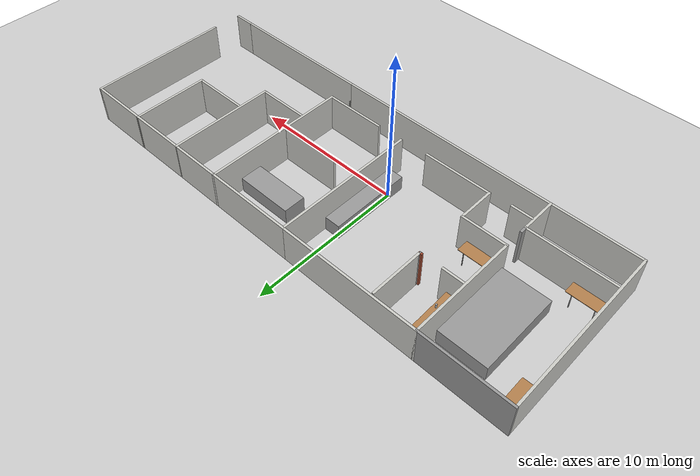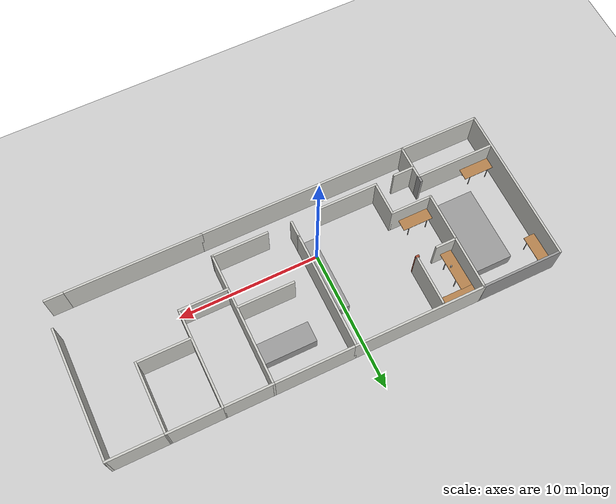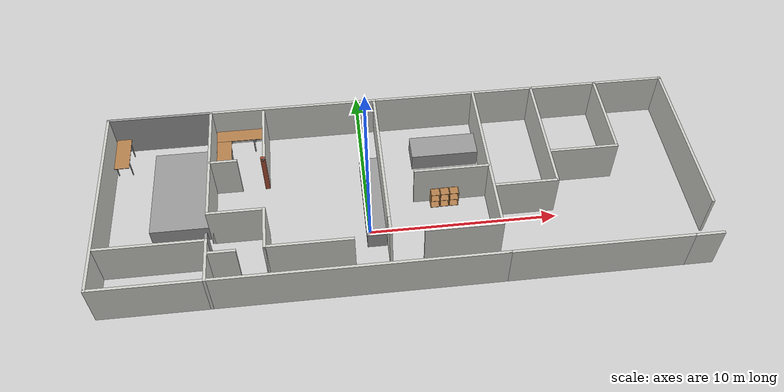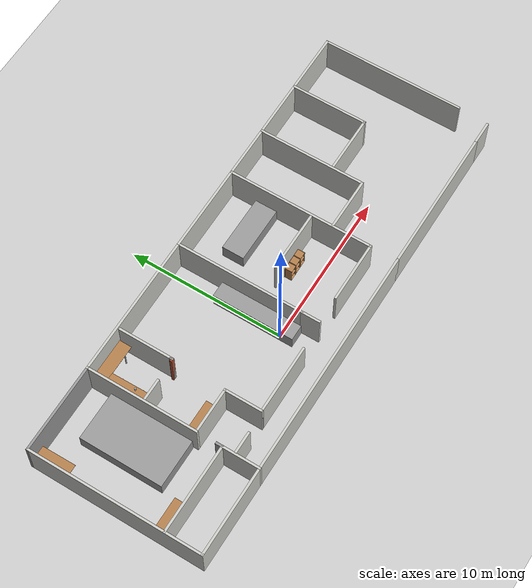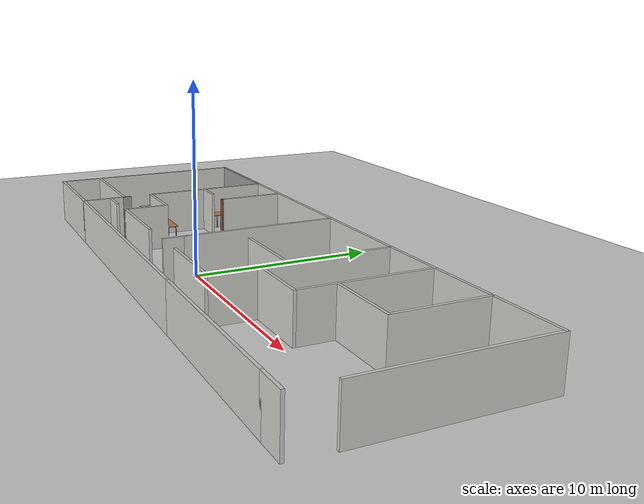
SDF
<sdf version="1.6">
 <world name="default">
  <light name="sun" type="directional">
   <pose>0 0 10 0 -0 0</pose>
   <diffuse>0.8 0.8 0.8 1</diffuse>
   <specular>0.2 0.2 0.2 1</specular>
   <attenuation>
    <range>1000</range>
    <constant>0.9</constant>
    <linear>0.01</linear>
    <quadratic>0.001</quadratic>
   </attenuation>
   <direction>-0.5 0.1 -0.9</direction>
  </light>
  <model name="ground_plane">
   <static>1</static>
   <link name="link">
    <collision name="collision">
     <geometry><plane><normal>0 0 1</normal><size>100 100</size></plane></geometry>
     <surface><friction><ode><mu>100</mu><mu2>50</mu2></ode></friction></surface>
    </collision>
    <visual name="visual">
     <cast_shadows>0</cast_shadows>
     <geometry><plane><normal>0 0 1</normal><size>100 100</size></plane></geometry>
     <material>
      <script><uri>file://media/materials/scripts/gazebo.material</uri><name>Gazebo/Grey</name></script>
     </material>
    </visual>
   </link>
  </model>
  <gravity>0 0 -9.8</gravity>
  <magnetic_field>6e-06 2.3e-05 -4.2e-05</magnetic_field>
  <atmosphere type="adiabatic"/>
  <physics name="default_physics" default="0" type="ode">
   <max_step_size>0.001</max_step_size>
   <real_time_factor>1</real_time_factor>
   <real_time_update_rate>1000</real_time_update_rate>
  </physics>
  <scene><ambient>0.4 0.4 0.4 1</ambient><background>0.7 0.7 0.7 1</background><shadows>1</shadows></scene>
  <audio><device>default</device></audio>
  <spherical_coordinates>
   <surface_model>EARTH_WGS84</surface_model>
   <latitude_deg>0</latitude_deg>
   <longitude_deg>0</longitude_deg>
   <elevation>0</elevation>
   <heading_deg>0</heading_deg>
  </spherical_coordinates>
  <model name="workplace">
   <pose>1.82011 1.79563 0 0 -0 0</pose>
   <link name="Wall_0">
    <collision name="Wall_0_Collision">
     <geometry><box><size>8.25 0.15 2.5</size></box></geometry>
     <pose>0 0 1.25 0 -0 0</pose>
    </collision>
    <visual name="Wall_0_Visual">
     <pose>0 0 1.25 0 -0 0</pose>
     <geometry><box><size>8.25 0.15 2.5</size></box></geometry>
     <material>
      <script><uri>file://media/materials/scripts/gazebo.material</uri><name>Gazebo/CeilingTiled</name></script>
      <ambient>1 1 1 1</ambient>
     </material>
     <meta><layer>0</layer></meta>
    </visual>
    <pose>-0.915173 1.35976 0 0 -0 1.5708</pose>
   </link>
   <link name="Wall_10">
    <collision name="Wall_10_Collision">
     <geometry><box><size>1.25 0.15 2.5</size></box></geometry>
     <pose>0 0 1.25 0 -0 0</pose>
    </collision>
    <visual name="Wall_10_Visual">
     <pose>0 0 1.25 0 -0 0</pose>
     <geometry><box><size>1.25 0.15 2.5</size></box></geometry>
     <material>
      <script><uri>file://media/materials/scripts/gazebo.material</uri><name>Gazebo/CeilingTiled</name></script>
      <ambient>1 1 1 1</ambient>
     </material>
     <meta><layer>0</layer></meta>
    </visual>
    <pose>-0.915173 -3.24024 0 0 -0 -1.5708</pose>
   </link>
   <link name="Wall_15">
    <collision name="Wall_15_Collision">
     <geometry><box><size>14.75 0.15 2.5</size></box></geometry>
     <pose>0 0 1.25 0 -0 0</pose>
    </collision>
    <visual name="Wall_15_Visual">
     <pose>0 0 1.25 0 -0 0</pose>
     <geometry><box><size>14.75 0.15 2.5</size></box></geometry>
     <material>
      <script><uri>file://media/materials/scripts/gazebo.material</uri><name>Gazebo/CeilingTiled</name></script>
      <ambient>1 1 1 1</ambient>
     </material>
     <meta><layer>0</layer></meta>
    </visual>
    <pose>-2.55759 -5.55178 0 0 -0 0</pose>
   </link>
   <link name="Wall_18">
    <collision name="Wall_18_Collision">
     <geometry><box><size>5.75 0.15 2.5</size></box></geometry>
     <pose>0 0 1.25 0 -0 0</pose>
    </collision>
    <visual name="Wall_18_Visual">
     <pose>0 0 1.25 0 -0 0</pose>
     <geometry><box><size>5.75 0.15 2.5</size></box></geometry>
     <material>
      <script><uri>file://media/materials/scripts/gazebo.material</uri><name>Gazebo/CeilingTiled</name></script>
      <ambient>1 1 1 1</ambient>
     </material>
     <meta><layer>0</layer></meta>
    </visual>
    <pose>1.90232 5.54454 0 0 -0 0</pose>
   </link>
   <link name="Wall_19">
    <collision name="Wall_19_Collision">
     <geometry><box><size>9.5 0.15 2.5</size></box></geometry>
     <pose>0 0 1.25 0 -0 0</pose>
    </collision>
    <visual name="Wall_19_Visual">
     <pose>0 0 1.25 0 -0 0</pose>
     <geometry><box><size>9.5 0.15 2.5</size></box></geometry>
     <material>
      <script><uri>file://media/materials/scripts/gazebo.material</uri><name>Gazebo/CeilingTiled</name></script>
      <ambient>1 1 1 1</ambient>
     </material>
     <meta><layer>0</layer></meta>
    </visual>
    <pose>4.70232 0.869544 0 0 -0 -1.5708</pose>
   </link>
   <link name="Wall_2">
    <collision name="Wall_2_Collision">
     <geometry><box><size>7.25 0.15 2.5</size></box></geometry>
     <pose>0 0 1.25 0 -0 0</pose>
    </collision>
    <visual name="Wall_2_Visual">
     <pose>0 0 1.25 0 -0 0</pose>
     <geometry><box><size>7.25 0.15 2.5</size></box></geometry>
     <material>
      <script><uri>file://media/materials/scripts/gazebo.material</uri><name>Gazebo/CeilingTiled</name></script>
      <ambient>1 1 1 1</ambient>
     </material>
     <meta><layer>0</layer></meta>
    </visual>
    <pose>-9.99768 1.99454 0 0 -0 -1.5708</pose>
   </link>
   <link name="Wall_20">
    <collision name="Wall_20_Collision">
     <geometry><box><size>4 0.15 2.5</size></box></geometry>
     <pose>0 0 1.25 0 -0 0</pose>
    </collision>
    <visual name="Wall_20_Visual">
     <pose>0 0 1.25 0 -0 0</pose>
     <geometry><box><size>4 0.15 2.5</size></box></geometry>
     <material>
      <script><uri>file://media/materials/scripts/gazebo.material</uri><name>Gazebo/CeilingTiled</name></script>
      <ambient>1 1 1 1</ambient>
     </material>
     <meta><layer>0</layer></meta>
    </visual>
    <pose>2.77732 -3.80546 0 0 -0 3.14159</pose>
   </link>
   <link name="Wall_22">
    <collision name="Wall_22_Collision">
     <geometry><box><size>4 0.15 2.5</size></box></geometry>
     <pose>0 0 1.25 0 -0 0</pose>
    </collision>
    <visual name="Wall_22_Visual">
     <pose>0 0 1.25 0 -0 0</pose>
     <geometry><box><size>4 0.15 2.5</size></box></geometry>
     <material>
      <script><uri>file://media/materials/scripts/gazebo.material</uri><name>Gazebo/CeilingTiled</name></script>
      <ambient>1 1 1 1</ambient>
     </material>
     <meta><layer>0</layer></meta>
    </visual>
    <pose>2.69206 0.076156 0 0 -0 3.14159</pose>
   </link>
   <link name="Wall_29">
    <collision name="Wall_29_Collision">
     <geometry><box><size>3.5 0.15 2.5</size></box></geometry>
     <pose>0 0 1.25 0 -0 0</pose>
    </collision>
    <visual name="Wall_29_Visual">
     <pose>0 0 1.25 0 -0 0</pose>
     <geometry><box><size>3.5 0.15 2.5</size></box></geometry>
     <material>
      <script><uri>file://media/materials/scripts/gazebo.material</uri><name>Gazebo/CeilingTiled</name></script>
      <ambient>1 1 1 1</ambient>
     </material>
     <meta><layer>0</layer></meta>
    </visual>
    <pose>-7.11284 3.66004 0 0 -0 1.5708</pose>
   </link>
   <link name="Wall_3">
    <collision name="Wall_3_Collision">
     <geometry><box><size>3 0.15 2.5</size></box></geometry>
     <pose>0 0 1.25 0 -0 0</pose>
    </collision>
    <visual name="Wall_3_Visual">
     <pose>0 0 1.25 0 -0 0</pose>
     <geometry><box><size>3 0.15 2.5</size></box></geometry>
     <material>
      <script><uri>file://media/materials/scripts/gazebo.material</uri><name>Gazebo/CeilingTiled</name></script>
      <ambient>1 1 1 1</ambient>
     </material>
     <meta><layer>0</layer></meta>
    </visual>
    <pose>-8.57268 -1.55546 0 0 -0 0</pose>
   </link>
   <link name="Wall_32">
    <collision name="Wall_32_Collision">
     <geometry><box><size>1.5 0.15 2.5</size></box></geometry>
     <pose>0 0 1.25 0 -0 0</pose>
    </collision>
    <visual name="Wall_32_Visual">
     <pose>0 0 1.25 0 -0 0</pose>
     <geometry><box><size>1.5 0.15 2.5</size></box></geometry>
     <material>
      <script><uri>file://media/materials/scripts/gazebo.material</uri><name>Gazebo/CeilingTiled</name></script>
      <ambient>1 1 1 1</ambient>
     </material>
     <meta><layer>0</layer></meta>
    </visual>
    <pose>-9.27823 1.85026 0 0 -0 0</pose>
   </link>
   <link name="Wall_39">
    <collision name="Wall_39_Collision">
     <geometry><box><size>0.25 0.15 2.5</size></box></geometry>
     <pose>0 0 1.25 0 -0 0</pose>
    </collision>
    <visual name="Wall_39_Visual">
     <pose>0 0 1.25 0 -0 0</pose>
     <geometry><box><size>0.25 0.15 2.5</size></box></geometry>
     <material>
      <script><uri>file://media/materials/scripts/gazebo.material</uri><name>Gazebo/Grey</name></script>
      <ambient>1 1 1 1</ambient>
     </material>
     <meta><layer>0</layer></meta>
    </visual>
    <pose>-7.11284 1.93504 0 0 -0 -1.5708</pose>
   </link>
   <link name="Wall_4">
    <collision name="Wall_4_Collision">
     <geometry><box><size>2.5 0.15 2.5</size></box></geometry>
     <pose>0 0 1.25 0 -0 0</pose>
    </collision>
    <visual name="Wall_4_Visual">
     <pose>0 0 1.25 0 -0 0</pose>
     <geometry><box><size>2.5 0.15 2.5</size></box></geometry>
     <material>
      <script><uri>file://media/materials/scripts/gazebo.material</uri><name>Gazebo/CeilingTiled</name></script>
      <ambient>1 1 1 1</ambient>
     </material>
     <meta><layer>0</layer></meta>
    </visual>
    <pose>-7.14768 -2.73046 0 0 -0 -1.5708</pose>
   </link>
   <link name="Wall_40">
    <collision name="Wall_40_Collision">
     <geometry><box><size>0.25 0.15 2.5</size></box></geometry>
     <pose>0 0 1.25 0 -0 0</pose>
    </collision>
    <visual name="Wall_40_Visual">
     <pose>0 0 1.25 0 -0 0</pose>
     <geometry><box><size>0.25 0.15 2.5</size></box></geometry>
     <material>
      <script><uri>file://media/materials/scripts/gazebo.material</uri><name>Gazebo/Bricks</name></script>
      <ambient>1 1 1 1</ambient>
     </material>
     <meta><layer>0</layer></meta>
    </visual>
    <pose>-7.16284 1.88504 0 0 -0 3.14159</pose>
   </link>
   <link name="Wall_5">
    <collision name="Wall_5_Collision">
     <geometry><box><size>4.5 0.15 2.5</size></box></geometry>
     <pose>0 0 1.25 0 -0 0</pose>
    </collision>
    <visual name="Wall_5_Visual">
     <pose>0 0 1.25 0 -0 0</pose>
     <geometry><box><size>4.5 0.15 2.5</size></box></geometry>
     <material>
      <script><uri>file://media/materials/scripts/gazebo.material</uri><name>Gazebo/CeilingTiled</name></script>
      <ambient>1 1 1 1</ambient>
     </material>
     <meta><layer>0</layer></meta>
    </visual>
    <pose>-4.97268 -3.90546 0 0 -0 0</pose>
   </link>
   <link name="Wall_59">
    <collision name="Wall_59_Collision">
     <geometry><box><size>5.75 0.15 2.5</size></box></geometry>
     <pose>0 0 1.25 0 -0 0</pose>
    </collision>
    <visual name="Wall_59_Visual">
     <pose>0 0 1.25 0 -0 0</pose>
     <geometry><box><size>5.75 0.15 2.5</size></box></geometry>
     <material>
      <script><uri>file://media/materials/scripts/gazebo.material</uri><name>Gazebo/Grey</name></script>
      <ambient>1 1 1 1</ambient>
     </material>
     <meta><layer>0</layer></meta>
    </visual>
    <pose>-12.7977 5.54454 0 0 -0 3.14159</pose>
   </link>
   <link name="Wall_60">
    <collision name="Wall_60_Collision">
     <geometry><box><size>11.25 0.15 2.5</size></box></geometry>
     <pose>0 0 1.25 0 -0 0</pose>
    </collision>
    <visual name="Wall_60_Visual">
     <pose>0 0 1.25 0 -0 0</pose>
     <geometry><box><size>11.25 0.15 2.5</size></box></geometry>
     <material>
      <script><uri>file://media/materials/scripts/gazebo.material</uri><name>Gazebo/CeilingTiled</name></script>
      <ambient>1 1 1 1</ambient>
     </material>
     <meta><layer>0</layer></meta>
    </visual>
    <pose>-15.5977 -0.005456 0 0 -0 -1.5708</pose>
   </link>
   <link name="Wall_61">
    <collision name="Wall_61_Collision">
     <geometry><box><size>5.75 0.15 2.5</size></box></geometry>
     <pose>0 0 1.25 0 -0 0</pose>
    </collision>
    <visual name="Wall_61_Visual">
     <pose>0 0 1.25 0 -0 0</pose>
     <geometry><box><size>5.75 0.15 2.5</size></box></geometry>
     <material>
      <script><uri>file://media/materials/scripts/gazebo.material</uri><name>Gazebo/CeilingTiled</name></script>
      <ambient>1 1 1 1</ambient>
     </material>
     <meta><layer>0</layer></meta>
    </visual>
    <pose>-12.7977 -5.55546 0 0 -0 0</pose>
   </link>
   <link name="Wall_62">
    <collision name="Wall_62_Collision">
     <geometry><box><size>2.5 0.15 2.5</size></box></geometry>
     <pose>0 0 1.25 0 -0 0</pose>
    </collision>
    <visual name="Wall_62_Visual">
     <pose>0 0 1.25 0 -0 0</pose>
     <geometry><box><size>2.5 0.15 2.5</size></box></geometry>
     <material>
      <script><uri>file://media/materials/scripts/gazebo.material</uri><name>Gazebo/CeilingTiled</name></script>
      <ambient>1 1 1 1</ambient>
     </material>
     <meta><layer>0</layer></meta>
    </visual>
    <pose>-9.99768 -4.38046 0 0 -0 1.5708</pose>
   </link>
   <link name="Wall_63">
    <collision name="Wall_63_Collision">
     <geometry><box><size>5.75 0.15 2.5</size></box></geometry>
     <pose>0 0 1.25 0 -0 0</pose>
    </collision>
    <visual name="Wall_63_Visual">
     <pose>0 0 1.25 0 -0 0</pose>
     <geometry><box><size>5.75 0.15 2.5</size></box></geometry>
     <material>
      <script><uri>file://media/materials/scripts/gazebo.material</uri><name>Gazebo/CeilingTiled</name></script>
      <ambient>1 1 1 1</ambient>
     </material>
     <meta><layer>0</layer></meta>
    </visual>
    <pose>-12.7977 -3.20546 0 0 -0 3.14159</pose>
   </link>
   <link name="Wall_65">
    <collision name="Wall_65_Collision">
     <geometry><box><size>1.5 0.15 2.5</size></box></geometry>
     <pose>0 0 1.25 0 -0 0</pose>
    </collision>
    <visual name="Wall_65_Visual">
     <pose>0 0 1.25 0 -0 0</pose>
     <geometry><box><size>1.5 0.15 2.5</size></box></geometry>
     <material>
      <script><uri>file://media/materials/scripts/gazebo.material</uri><name>Gazebo/CeilingTiled</name></script>
      <ambient>1 1 1 1</ambient>
     </material>
     <meta><layer>0</layer></meta>
    </visual>
    <pose>-9.27951 -3.98773 0 0 -0 0</pose>
   </link>
   <link name="Wall_68">
    <collision name="Wall_68_Collision">
     <geometry><box><size>0.5 0.15 2.5</size></box></geometry>
     <pose>0 0 1.25 0 -0 0</pose>
    </collision>
    <visual name="Wall_68_Visual">
     <pose>0 0 1.25 0 -0 0</pose>
     <geometry><box><size>0.5 0.15 2.5</size></box></geometry>
     <material>
      <script><uri>file://media/materials/scripts/gazebo.material</uri><name>Gazebo/Grey</name></script>
      <ambient>1 1 1 1</ambient>
     </material>
     <meta><layer>0</layer></meta>
    </visual>
    <pose>-9.99768 -3.03046 0 0 -0 1.5708</pose>
   </link>
   <link name="Wall_70">
    <collision name="Wall_70_Collision">
     <geometry><box><size>3.5 0.15 2.5</size></box></geometry>
     <pose>0 0 1.25 0 -0 0</pose>
    </collision>
    <visual name="Wall_70_Visual">
     <pose>0 0 1.25 0 -0 0</pose>
     <geometry><box><size>3.5 0.15 2.5</size></box></geometry>
     <material>
      <script><uri>file://media/materials/scripts/gazebo.material</uri><name>Gazebo/CeilingTiled</name></script>
      <ambient>1 1 1 1</ambient>
     </material>
     <meta><layer>0</layer></meta>
    </visual>
    <pose>6.37732 5.54454 0 0 -0 0</pose>
   </link>
   <link name="Wall_73">
    <collision name="Wall_73_Collision">
     <geometry><box><size>7 0.15 2.5</size></box></geometry>
     <pose>0 0 1.25 0 -0 0</pose>
    </collision>
    <visual name="Wall_73_Visual">
     <pose>0 0 1.25 0 -0 0</pose>
     <geometry><box><size>7 0.15 2.5</size></box></geometry>
     <material>
      <script><uri>file://media/materials/scripts/gazebo.material</uri><name>Gazebo/CeilingTiled</name></script>
      <ambient>1 1 1 1</ambient>
     </material>
     <meta><layer>0</layer></meta>
    </visual>
    <pose>8.05232 2.11954 0 0 -0 -1.5708</pose>
   </link>
   <link name="Wall_76">
    <collision name="Wall_76_Collision">
     <geometry><box><size>3.5 0.15 2.5</size></box></geometry>
     <pose>0 0 1.25 0 -0 0</pose>
    </collision>
    <visual name="Wall_76_Visual">
     <pose>0 0 1.25 0 -0 0</pose>
     <geometry><box><size>3.5 0.15 2.5</size></box></geometry>
     <material>
      <script><uri>file://media/materials/scripts/gazebo.material</uri><name>Gazebo/CeilingTiled</name></script>
      <ambient>1 1 1 1</ambient>
     </material>
     <meta><layer>0</layer></meta>
    </visual>
    <pose>6.37732 -1.30546 0 0 -0 3.14159</pose>
   </link>
   <link name="Wall_78">
    <collision name="Wall_78_Collision">
     <geometry><box><size>9.5 0.15 2.5</size></box></geometry>
     <pose>0 0 1.25 0 -0 0</pose>
    </collision>
    <visual name="Wall_78_Visual">
     <pose>0 0 1.25 0 -0 0</pose>
     <geometry><box><size>9.5 0.15 2.5</size></box></geometry>
     <material>
      <script><uri>file://media/materials/scripts/gazebo.material</uri><name>Gazebo/CeilingTiled</name></script>
      <ambient>1 1 1 1</ambient>
     </material>
     <meta><layer>0</layer></meta>
    </visual>
    <pose>9.41741 -5.55178 0 0 -0 0</pose>
   </link>
   <link name="Wall_8">
    <collision name="Wall_8_Collision">
     <geometry><box><size>9.25 0.15 2.5</size></box></geometry>
     <pose>0 0 1.25 0 -0 0</pose>
    </collision>
    <visual name="Wall_8_Visual">
     <pose>0 0 1.25 0 -0 0</pose>
     <geometry><box><size>9.25 0.15 2.5</size></box></geometry>
     <material>
      <script><uri>file://media/materials/scripts/gazebo.material</uri><name>Gazebo/CeilingTiled</name></script>
      <ambient>1 1 1 1</ambient>
     </material>
     <meta><layer>0</layer></meta>
    </visual>
    <pose>-5.44768 5.54454 0 0 -0 0</pose>
   </link>
   <link name="Wall_82">
    <collision name="Wall_82_Collision">
     <geometry><box><size>3.75 0.15 2.5</size></box></geometry>
     <pose>0 0 1.25 0 -0 0</pose>
    </collision>
    <visual name="Wall_82_Visual">
     <pose>0 0 1.25 0 -0 0</pose>
     <geometry><box><size>3.75 0.15 2.5</size></box></geometry>
     <material>
      <script><uri>file://media/materials/scripts/gazebo.material</uri><name>Gazebo/CeilingTiled</name></script>
      <ambient>1 1 1 1</ambient>
     </material>
     <meta><layer>0</layer></meta>
    </visual>
    <pose>9.94768 0.70524 0 0 -0 0</pose>
   </link>
   <link name="Wall_83">
    <collision name="Wall_83_Collision">
     <geometry><box><size>5 0.15 2.5</size></box></geometry>
     <pose>0 0 1.25 0 -0 0</pose>
    </collision>
    <visual name="Wall_83_Visual">
     <pose>0 0 1.25 0 -0 0</pose>
     <geometry><box><size>5 0.15 2.5</size></box></geometry>
     <material>
      <script><uri>file://media/materials/scripts/gazebo.material</uri><name>Gazebo/CeilingTiled</name></script>
      <ambient>1 1 1 1</ambient>
     </material>
     <meta><layer>0</layer></meta>
    </visual>
    <pose>11.7477 3.13024 0 0 -0 1.5708</pose>
   </link>
   <link name="Wall_84">
    <collision name="Wall_84_Collision">
     <geometry><box><size>3.84538 0.15 2.5</size></box></geometry>
     <pose>0 0 1.25 0 -0 0</pose>
    </collision>
    <visual name="Wall_84_Visual">
     <pose>0 0 1.25 0 -0 0</pose>
     <geometry><box><size>3.84538 0.15 2.5</size></box></geometry>
     <material>
      <script><uri>file://media/materials/scripts/gazebo.material</uri><name>Gazebo/CeilingTiled</name></script>
      <ambient>1 1 1 1</ambient>
     </material>
     <meta><layer>0</layer></meta>
    </visual>
    <pose>9.9 5.54989 0 0 -0 -3.1387</pose>
   </link>
   <link name="Wall_89">
    <collision name="Wall_89_Collision">
     <geometry><box><size>4 0.15 2.5</size></box></geometry>
     <pose>0 0 1.25 0 -0 0</pose>
    </collision>
    <visual name="Wall_89_Visual">
     <pose>0 0 1.25 0 -0 0</pose>
     <geometry><box><size>4 0.15 2.5</size></box></geometry>
     <material>
      <script><uri>file://media/materials/scripts/gazebo.material</uri><name>Gazebo/CeilingTiled</name></script>
      <ambient>1 1 1 1</ambient>
     </material>
     <meta><layer>0</layer></meta>
    </visual>
    <pose>13.6727 5.55524 0 0 -0 0</pose>
   </link>
   <link name="Wall_90">
    <collision name="Wall_90_Collision">
     <geometry><box><size>9.25 0.15 2.5</size></box></geometry>
     <pose>0 0 1.25 0 -0 0</pose>
    </collision>
    <visual name="Wall_90_Visual">
     <pose>0 0 1.25 0 -0 0</pose>
     <geometry><box><size>9.25 0.15 2.5</size></box></geometry>
     <material>
      <script><uri>file://media/materials/scripts/gazebo.material</uri><name>Gazebo/CeilingTiled</name></script>
      <ambient>1 1 1 1</ambient>
     </material>
     <meta><layer>0</layer></meta>
    </visual>
    <pose>15.5977 1.00524 0 0 -0 -1.5708</pose>
   </link>
   <link name="Wall_92">
    <collision name="Wall_92_Collision">
     <geometry><box><size>1.5 0.15 2.5</size></box></geometry>
     <pose>0 0 1.25 0 -0 0</pose>
    </collision>
    <visual name="Wall_92_Visual">
     <pose>0 0 1.25 0 -0 0</pose>
     <geometry><box><size>1.5 0.15 2.5</size></box></geometry>
     <material>
      <script><uri>file://media/materials/scripts/gazebo.material</uri><name>Gazebo/CeilingTiled</name></script>
      <ambient>1 1 1 1</ambient>
     </material>
     <meta><layer>0</layer></meta>
    </visual>
    <pose>14.7674 -5.55178 0 0 -0 0</pose>
   </link>
   <static>1</static>
  </model>
  <model name="table">
   <link name="link">
    <pose>0.29068 0 0 0 -0 0</pose>
    <inertial>
     <inertia><ixx>0</ixx><ixy>0</ixy><ixz>0</ixz><iyy>0</iyy><iyz>0</iyz><izz>0</izz></inertia>
     <mass>0</mass>
    </inertial>
    <visual name="front_left_leg">
     <pose>0.68 0.38 0.5 0 -0 0</pose>
     <geometry><cylinder><radius>0.0286498</radius><length>1</length></cylinder></geometry>
     <material>
      <script><uri>file://media/materials/scripts/gazebo.material</uri><name>Gazebo/Grey</name></script>
     </material>
    </visual>
    <visual name="back_right_leg">
     <pose>-0.68 -0.38 0.5 0 -0 0</pose>
     <geometry><cylinder><radius>0.0286498</radius><length>1</length></cylinder></geometry>
     <material>
      <script><uri>file://media/materials/scripts/gazebo.material</uri><name>Gazebo/Grey</name></script>
     </material>
    </visual>
    <visual name="back_left_leg">
     <pose>-0.68 0.38 0.5 0 -0 0</pose>
     <geometry><cylinder><radius>0.0286498</radius><length>1</length></cylinder></geometry>
     <material>
      <script><uri>file://media/materials/scripts/gazebo.material</uri><name>Gazebo/Grey</name></script>
     </material>
    </visual>
    <visual name="front_right_leg">
     <pose>0.68 -0.38 0.5 0 -0 0</pose>
     <geometry><cylinder><radius>0.0286498</radius><length>1</length></cylinder></geometry>
     <material>
      <script><uri>file://media/materials/scripts/gazebo.material</uri><name>Gazebo/Grey</name></script>
     </material>
    </visual>
    <visual name="visual1">
     <pose>0 0 1 0 -0 0</pose>
     <geometry><box><size>2.14873 0.8 0.03</size></box></geometry>
     <material>
      <script><uri>file://media/materials/scripts/gazebo.material</uri><name>Gazebo/Wood</name></script>
     </material>
    </visual>
    <collision name="front_left_leg">
     <pose>0.68 0.38 0.5 0 -0 0</pose>
     <geometry><cylinder><radius>0.02865</radius><length>1</length></cylinder></geometry>
     <surface>
      <friction>
       <ode><mu>1</mu><mu2>1</mu2><fdir1>0 0 0</fdir1><slip1>0</slip1><slip2>0</slip2></ode>
       <torsional>
        <coefficient>1</coefficient>
        <patch_radius>0</patch_radius>
        <surface_radius>0</surface_radius>
        <use_patch_radius>1</use_patch_radius>
        <ode><slip>0</slip></ode>
       </torsional>
      </friction>
      <bounce><restitution_coefficient>0</restitution_coefficient><threshold>1e+06</threshold></bounce>
      <contact>
       <collide_without_contact>0</collide_without_contact>
       <collide_without_contact_bitmask>1</collide_without_contact_bitmask>
       <collide_bitmask>1</collide_bitmask>
       <ode>
        <soft_cfm>0</soft_cfm>
        <soft_erp>0.2</soft_erp>
        <kp>1e+13</kp>
        <kd>1</kd>
        <max_vel>0.01</max_vel>
        <min_depth>0</min_depth>
       </ode>
       <bullet>
        <split_impulse>1</split_impulse>
        <split_impulse_penetration_threshold>-0.01</split_impulse_penetration_threshold>
        <soft_cfm>0</soft_cfm>
        <soft_erp>0.2</soft_erp>
        <kp>1e+13</kp>
        <kd>1</kd>
       </bullet>
      </contact>
     </surface>
    </collision>
    <collision name="front_right_leg">
     <pose>0.68 -0.38 0.5 0 -0 0</pose>
     <geometry><cylinder><radius>0.02865</radius><length>1</length></cylinder></geometry>
     <surface>
      <friction>
       <ode><mu>1</mu><mu2>1</mu2><fdir1>0 0 0</fdir1><slip1>0</slip1><slip2>0</slip2></ode>
       <torsional>
        <coefficient>1</coefficient>
        <patch_radius>0</patch_radius>
        <surface_radius>0</surface_radius>
        <use_patch_radius>1</use_patch_radius>
        <ode><slip>0</slip></ode>
       </torsional>
      </friction>
      <bounce><restitution_coefficient>0</restitution_coefficient><threshold>1e+06</threshold></bounce>
      <contact>
       <collide_without_contact>0</collide_without_contact>
       <collide_without_contact_bitmask>1</collide_without_contact_bitmask>
       <collide_bitmask>1</collide_bitmask>
       <ode>
        <soft_cfm>0</soft_cfm>
        <soft_erp>0.2</soft_erp>
        <kp>1e+13</kp>
        <kd>1</kd>
        <max_vel>0.01</max_vel>
        <min_depth>0</min_depth>
       </ode>
       <bullet>
        <split_impulse>1</split_impulse>
        <split_impulse_penetration_threshold>-0.01</split_impulse_penetration_threshold>
        <soft_cfm>0</soft_cfm>
        <soft_erp>0.2</soft_erp>
        <kp>1e+13</kp>
        <kd>1</kd>
       </bullet>
      </contact>
     </surface>
    </collision>
    <collision name="back_right_leg">
     <pose>-0.68 -0.38 0.5 0 -0 0</pose>
     <geometry><cylinder><radius>0.02865</radius><length>1</length></cylinder></geometry>
     <surface>
      <friction>
       <ode><mu>1</mu><mu2>1</mu2><fdir1>0 0 0</fdir1><slip1>0</slip1><slip2>0</slip2></ode>
       <torsional>
        <coefficient>1</coefficient>
        <patch_radius>0</patch_radius>
        <surface_radius>0</surface_radius>
        <use_patch_radius>1</use_patch_radius>
        <ode><slip>0</slip></ode>
       </torsional>
      </friction>
      <bounce><restitution_coefficient>0</restitution_coefficient><threshold>1e+06</threshold></bounce>
      <contact>
       <collide_without_contact>0</collide_without_contact>
       <collide_without_contact_bitmask>1</collide_without_contact_bitmask>
       <collide_bitmask>1</collide_bitmask>
       <ode>
        <soft_cfm>0</soft_cfm>
        <soft_erp>0.2</soft_erp>
        <kp>1e+13</kp>
        <kd>1</kd>
        <max_vel>0.01</max_vel>
        <min_depth>0</min_depth>
       </ode>
       <bullet>
        <split_impulse>1</split_impulse>
        <split_impulse_penetration_threshold>-0.01</split_impulse_penetration_threshold>
        <soft_cfm>0</soft_cfm>
        <soft_erp>0.2</soft_erp>
        <kp>1e+13</kp>
        <kd>1</kd>
       </bullet>
      </contact>
     </surface>
    </collision>
    <collision name="back_left_leg">
     <pose>-0.68 0.38 0.5 0 -0 0</pose>
     <geometry><cylinder><radius>0.02865</radius><length>1</length></cylinder></geometry>
     <surface>
      <friction>
       <ode><mu>1</mu><mu2>1</mu2><fdir1>0 0 0</fdir1><slip1>0</slip1><slip2>0</slip2></ode>
       <torsional>
        <coefficient>1</coefficient>
        <patch_radius>0</patch_radius>
        <surface_radius>0</surface_radius>
        <use_patch_radius>1</use_patch_radius>
        <ode><slip>0</slip></ode>
       </torsional>
      </friction>
      <bounce><restitution_coefficient>0</restitution_coefficient><threshold>1e+06</threshold></bounce>
      <contact>
       <collide_without_contact>0</collide_without_contact>
       <collide_without_contact_bitmask>1</collide_without_contact_bitmask>
       <collide_bitmask>1</collide_bitmask>
       <ode>
        <soft_cfm>0</soft_cfm>
        <soft_erp>0.2</soft_erp>
        <kp>1e+13</kp>
        <kd>1</kd>
        <max_vel>0.01</max_vel>
        <min_depth>0</min_depth>
       </ode>
       <bullet>
        <split_impulse>1</split_impulse>
        <split_impulse_penetration_threshold>-0.01</split_impulse_penetration_threshold>
        <soft_cfm>0</soft_cfm>
        <soft_erp>0.2</soft_erp>
        <kp>1e+13</kp>
        <kd>1</kd>
       </bullet>
      </contact>
     </surface>
    </collision>
    <collision name="surface">
     <pose>0 0 1 0 -0 0</pose>
     <geometry><box><size>2.14873 0.8 0.03</size></box></geometry>
     <surface>
      <friction>
       <ode><mu>0.6</mu><mu2>0.6</mu2><fdir1>0 0 0</fdir1><slip1>0</slip1><slip2>0</slip2></ode>
       <torsional>
        <coefficient>1</coefficient>
        <patch_radius>0</patch_radius>
        <surface_radius>0</surface_radius>
        <use_patch_radius>1</use_patch_radius>
        <ode><slip>0</slip></ode>
       </torsional>
      </friction>
      <bounce><restitution_coefficient>0</restitution_coefficient><threshold>1e+06</threshold></bounce>
      <contact>
       <collide_without_contact>0</collide_without_contact>
       <collide_without_contact_bitmask>1</collide_without_contact_bitmask>
       <collide_bitmask>1</collide_bitmask>
       <ode>
        <soft_cfm>0</soft_cfm>
        <soft_erp>0.2</soft_erp>
        <kp>1e+13</kp>
        <kd>1</kd>
        <max_vel>0.01</max_vel>
        <min_depth>0</min_depth>
       </ode>
       <bullet>
        <split_impulse>1</split_impulse>
        <split_impulse_penetration_threshold>-0.01</split_impulse_penetration_threshold>
        <soft_cfm>0</soft_cfm>
        <soft_erp>0.2</soft_erp>
        <kp>1e+13</kp>
        <kd>1</kd>
       </bullet>
      </contact>
     </surface>
    </collision>
   </link>
   <static>1</static>
   <pose>-7.26339 0.73651 0 0 -0 0</pose>
  </model>
  <model name="table_clone">
   <link name="link">
    <pose>0.29068 0 0 0 -0 0</pose>
    <inertial>
     <inertia><ixx>0</ixx><ixy>0</ixy><ixz>0</ixz><iyy>0</iyy><iyz>0</iyz><izz>0</izz></inertia>
     <mass>0</mass>
    </inertial>
    <visual name="back_left_leg">
     <pose>-0.68 0.38 0.5 0 -0 0</pose>
     <geometry><cylinder><radius>0.0363517</radius><length>1</length></cylinder></geometry>
     <material>
      <script><uri>file://media/materials/scripts/gazebo.material</uri><name>Gazebo/Grey</name></script>
     </material>
    </visual>
    <visual name="front_right_leg">
     <pose>0.68 -0.38 0.5 0 -0 0</pose>
     <geometry><cylinder><radius>0.0363517</radius><length>1</length></cylinder></geometry>
     <material>
      <script><uri>file://media/materials/scripts/gazebo.material</uri><name>Gazebo/Grey</name></script>
     </material>
    </visual>
    <visual name="back_right_leg">
     <pose>-0.68 -0.38 0.5 0 -0 0</pose>
     <geometry><cylinder><radius>0.0363517</radius><length>1</length></cylinder></geometry>
     <material>
      <script><uri>file://media/materials/scripts/gazebo.material</uri><name>Gazebo/Grey</name></script>
     </material>
    </visual>
    <visual name="front_left_leg">
     <pose>0.68 0.38 0.5 0 -0 0</pose>
     <geometry><cylinder><radius>0.0363517</radius><length>1</length></cylinder></geometry>
     <material>
      <script><uri>file://media/materials/scripts/gazebo.material</uri><name>Gazebo/Grey</name></script>
     </material>
    </visual>
    <visual name="visual1">
     <pose>0 0 1 0 -0 0</pose>
     <geometry><box><size>2.76183 0.8 0.03</size></box></geometry>
     <material>
      <script><uri>file://media/materials/scripts/gazebo.material</uri><name>Gazebo/Wood</name></script>
     </material>
    </visual>
    <collision name="front_left_leg">
     <pose>0.68 0.38 0.5 0 -0 0</pose>
     <geometry><cylinder><radius>0.036352</radius><length>1</length></cylinder></geometry>
     <surface>
      <friction>
       <ode><mu>1</mu><mu2>1</mu2><fdir1>0 0 0</fdir1><slip1>0</slip1><slip2>0</slip2></ode>
       <torsional>
        <coefficient>1</coefficient>
        <patch_radius>0</patch_radius>
        <surface_radius>0</surface_radius>
        <use_patch_radius>1</use_patch_radius>
        <ode><slip>0</slip></ode>
       </torsional>
      </friction>
      <bounce><restitution_coefficient>0</restitution_coefficient><threshold>1e+06</threshold></bounce>
      <contact>
       <collide_without_contact>0</collide_without_contact>
       <collide_without_contact_bitmask>1</collide_without_contact_bitmask>
       <collide_bitmask>1</collide_bitmask>
       <ode>
        <soft_cfm>0</soft_cfm>
        <soft_erp>0.2</soft_erp>
        <kp>1e+13</kp>
        <kd>1</kd>
        <max_vel>0.01</max_vel>
        <min_depth>0</min_depth>
       </ode>
       <bullet>
        <split_impulse>1</split_impulse>
        <split_impulse_penetration_threshold>-0.01</split_impulse_penetration_threshold>
        <soft_cfm>0</soft_cfm>
        <soft_erp>0.2</soft_erp>
        <kp>1e+13</kp>
        <kd>1</kd>
       </bullet>
      </contact>
     </surface>
    </collision>
    <collision name="front_right_leg">
     <pose>0.68 -0.38 0.5 0 -0 0</pose>
     <geometry><cylinder><radius>0.036352</radius><length>1</length></cylinder></geometry>
     <surface>
      <friction>
       <ode><mu>1</mu><mu2>1</mu2><fdir1>0 0 0</fdir1><slip1>0</slip1><slip2>0</slip2></ode>
       <torsional>
        <coefficient>1</coefficient>
        <patch_radius>0</patch_radius>
        <surface_radius>0</surface_radius>
        <use_patch_radius>1</use_patch_radius>
        <ode><slip>0</slip></ode>
       </torsional>
      </friction>
      <bounce><restitution_coefficient>0</restitution_coefficient><threshold>1e+06</threshold></bounce>
      <contact>
       <collide_without_contact>0</collide_without_contact>
       <collide_without_contact_bitmask>1</collide_without_contact_bitmask>
       <collide_bitmask>1</collide_bitmask>
       <ode>
        <soft_cfm>0</soft_cfm>
        <soft_erp>0.2</soft_erp>
        <kp>1e+13</kp>
        <kd>1</kd>
        <max_vel>0.01</max_vel>
        <min_depth>0</min_depth>
       </ode>
       <bullet>
        <split_impulse>1</split_impulse>
        <split_impulse_penetration_threshold>-0.01</split_impulse_penetration_threshold>
        <soft_cfm>0</soft_cfm>
        <soft_erp>0.2</soft_erp>
        <kp>1e+13</kp>
        <kd>1</kd>
       </bullet>
      </contact>
     </surface>
    </collision>
    <collision name="back_right_leg">
     <pose>-0.68 -0.38 0.5 0 -0 0</pose>
     <geometry><cylinder><radius>0.036352</radius><length>1</length></cylinder></geometry>
     <surface>
      <friction>
       <ode><mu>1</mu><mu2>1</mu2><fdir1>0 0 0</fdir1><slip1>0</slip1><slip2>0</slip2></ode>
       <torsional>
        <coefficient>1</coefficient>
        <patch_radius>0</patch_radius>
        <surface_radius>0</surface_radius>
        <use_patch_radius>1</use_patch_radius>
        <ode><slip>0</slip></ode>
       </torsional>
      </friction>
      <bounce><restitution_coefficient>0</restitution_coefficient><threshold>1e+06</threshold></bounce>
      <contact>
       <collide_without_contact>0</collide_without_contact>
       <collide_without_contact_bitmask>1</collide_without_contact_bitmask>
       <collide_bitmask>1</collide_bitmask>
       <ode>
        <soft_cfm>0</soft_cfm>
        <soft_erp>0.2</soft_erp>
        <kp>1e+13</kp>
        <kd>1</kd>
        <max_vel>0.01</max_vel>
        <min_depth>0</min_depth>
       </ode>
       <bullet>
        <split_impulse>1</split_impulse>
        <split_impulse_penetration_threshold>-0.01</split_impulse_penetration_threshold>
        <soft_cfm>0</soft_cfm>
        <soft_erp>0.2</soft_erp>
        <kp>1e+13</kp>
        <kd>1</kd>
       </bullet>
      </contact>
     </surface>
    </collision>
    <collision name="back_left_leg">
     <pose>-0.68 0.38 0.5 0 -0 0</pose>
     <geometry><cylinder><radius>0.036352</radius><length>1</length></cylinder></geometry>
     <surface>
      <friction>
       <ode><mu>1</mu><mu2>1</mu2><fdir1>0 0 0</fdir1><slip1>0</slip1><slip2>0</slip2></ode>
       <torsional>
        <coefficient>1</coefficient>
        <patch_radius>0</patch_radius>
        <surface_radius>0</surface_radius>
        <use_patch_radius>1</use_patch_radius>
        <ode><slip>0</slip></ode>
       </torsional>
      </friction>
      <bounce><restitution_coefficient>0</restitution_coefficient><threshold>1e+06</threshold></bounce>
      <contact>
       <collide_without_contact>0</collide_without_contact>
       <collide_without_contact_bitmask>1</collide_without_contact_bitmask>
       <collide_bitmask>1</collide_bitmask>
       <ode>
        <soft_cfm>0</soft_cfm>
        <soft_erp>0.2</soft_erp>
        <kp>1e+13</kp>
        <kd>1</kd>
        <max_vel>0.01</max_vel>
        <min_depth>0</min_depth>
       </ode>
       <bullet>
        <split_impulse>1</split_impulse>
        <split_impulse_penetration_threshold>-0.01</split_impulse_penetration_threshold>
        <soft_cfm>0</soft_cfm>
        <soft_erp>0.2</soft_erp>
        <kp>1e+13</kp>
        <kd>1</kd>
       </bullet>
      </contact>
     </surface>
    </collision>
    <collision name="surface">
     <pose>0 0 1 0 -0 0</pose>
     <geometry><box><size>2.76183 0.8 0.03</size></box></geometry>
     <surface>
      <friction>
       <ode><mu>0.6</mu><mu2>0.6</mu2><fdir1>0 0 0</fdir1><slip1>0</slip1><slip2>0</slip2></ode>
       <torsional>
        <coefficient>1</coefficient>
        <patch_radius>0</patch_radius>
        <surface_radius>0</surface_radius>
        <use_patch_radius>1</use_patch_radius>
        <ode><slip>0</slip></ode>
       </torsional>
      </friction>
      <bounce><restitution_coefficient>0</restitution_coefficient><threshold>1e+06</threshold></bounce>
      <contact>
       <collide_without_contact>0</collide_without_contact>
       <collide_without_contact_bitmask>1</collide_without_contact_bitmask>
       <collide_bitmask>1</collide_bitmask>
       <ode>
        <soft_cfm>0</soft_cfm>
        <soft_erp>0.2</soft_erp>
        <kp>1e+13</kp>
        <kd>1</kd>
        <max_vel>0.01</max_vel>
        <min_depth>0</min_depth>
       </ode>
       <bullet>
        <split_impulse>1</split_impulse>
        <split_impulse_penetration_threshold>-0.01</split_impulse_penetration_threshold>
        <soft_cfm>0</soft_cfm>
        <soft_erp>0.2</soft_erp>
        <kp>1e+13</kp>
        <kd>1</kd>
       </bullet>
      </contact>
     </surface>
    </collision>
   </link>
   <static>1</static>
   <pose>-6.96854 6.8597 0 0 -0 0</pose>
  </model>
  <model name="table_clone_clone">
   <link name="link">
    <pose>0.29068 0 0 0 -0 0</pose>
    <inertial>
     <inertia><ixx>0</ixx><ixy>0</ixy><ixz>0</ixz><iyy>0</iyy><iyz>0</iyz><izz>0</izz></inertia>
     <mass>0</mass>
    </inertial>
    <visual name="back_left_leg">
     <pose>-0.68 0.38 0.5 0 -0 0</pose>
     <geometry><cylinder><radius>0.0363517</radius><length>1</length></cylinder></geometry>
     <material>
      <script><uri>file://media/materials/scripts/gazebo.material</uri><name>Gazebo/Grey</name></script>
     </material>
    </visual>
    <visual name="front_right_leg">
     <pose>0.68 -0.38 0.5 0 -0 0</pose>
     <geometry><cylinder><radius>0.0363517</radius><length>1</length></cylinder></geometry>
     <material>
      <script><uri>file://media/materials/scripts/gazebo.material</uri><name>Gazebo/Grey</name></script>
     </material>
    </visual>
    <visual name="back_right_leg">
     <pose>-0.68 -0.38 0.5 0 -0 0</pose>
     <geometry><cylinder><radius>0.0363517</radius><length>1</length></cylinder></geometry>
     <material>
      <script><uri>file://media/materials/scripts/gazebo.material</uri><name>Gazebo/Grey</name></script>
     </material>
    </visual>
    <visual name="front_left_leg">
     <pose>0.68 0.38 0.5 0 -0 0</pose>
     <geometry><cylinder><radius>0.0363517</radius><length>1</length></cylinder></geometry>
     <material>
      <script><uri>file://media/materials/scripts/gazebo.material</uri><name>Gazebo/Grey</name></script>
     </material>
    </visual>
    <visual name="visual1">
     <pose>0 0 1 0 -0 0</pose>
     <geometry><box><size>2.76183 0.8 0.03</size></box></geometry>
     <material>
      <script><uri>file://media/materials/scripts/gazebo.material</uri><name>Gazebo/Wood</name></script>
     </material>
    </visual>
    <collision name="front_left_leg">
     <pose>0.68 0.38 0.5 0 -0 0</pose>
     <geometry><cylinder><radius>0.036352</radius><length>1</length></cylinder></geometry>
     <surface>
      <friction>
       <ode><mu>1</mu><mu2>1</mu2><fdir1>0 0 0</fdir1><slip1>0</slip1><slip2>0</slip2></ode>
       <torsional>
        <coefficient>1</coefficient>
        <patch_radius>0</patch_radius>
        <surface_radius>0</surface_radius>
        <use_patch_radius>1</use_patch_radius>
        <ode><slip>0</slip></ode>
       </torsional>
      </friction>
      <bounce><restitution_coefficient>0</restitution_coefficient><threshold>1e+06</threshold></bounce>
      <contact>
       <collide_without_contact>0</collide_without_contact>
       <collide_without_contact_bitmask>1</collide_without_contact_bitmask>
       <collide_bitmask>1</collide_bitmask>
       <ode>
        <soft_cfm>0</soft_cfm>
        <soft_erp>0.2</soft_erp>
        <kp>1e+13</kp>
        <kd>1</kd>
        <max_vel>0.01</max_vel>
        <min_depth>0</min_depth>
       </ode>
       <bullet>
        <split_impulse>1</split_impulse>
        <split_impulse_penetration_threshold>-0.01</split_impulse_penetration_threshold>
        <soft_cfm>0</soft_cfm>
        <soft_erp>0.2</soft_erp>
        <kp>1e+13</kp>
        <kd>1</kd>
       </bullet>
      </contact>
     </surface>
    </collision>
    <collision name="front_right_leg">
     <pose>0.68 -0.38 0.5 0 -0 0</pose>
     <geometry><cylinder><radius>0.036352</radius><length>1</length></cylinder></geometry>
     <surface>
      <friction>
       <ode><mu>1</mu><mu2>1</mu2><fdir1>0 0 0</fdir1><slip1>0</slip1><slip2>0</slip2></ode>
       <torsional>
        <coefficient>1</coefficient>
        <patch_radius>0</patch_radius>
        <surface_radius>0</surface_radius>
        <use_patch_radius>1</use_patch_radius>
        <ode><slip>0</slip></ode>
       </torsional>
      </friction>
      <bounce><restitution_coefficient>0</restitution_coefficient><threshold>1e+06</threshold></bounce>
      <contact>
       <collide_without_contact>0</collide_without_contact>
       <collide_without_contact_bitmask>1</collide_without_contact_bitmask>
       <collide_bitmask>1</collide_bitmask>
       <ode>
        <soft_cfm>0</soft_cfm>
        <soft_erp>0.2</soft_erp>
        <kp>1e+13</kp>
        <kd>1</kd>
        <max_vel>0.01</max_vel>
        <min_depth>0</min_depth>
       </ode>
       <bullet>
        <split_impulse>1</split_impulse>
        <split_impulse_penetration_threshold>-0.01</split_impulse_penetration_threshold>
        <soft_cfm>0</soft_cfm>
        <soft_erp>0.2</soft_erp>
        <kp>1e+13</kp>
        <kd>1</kd>
       </bullet>
      </contact>
     </surface>
    </collision>
    <collision name="back_right_leg">
     <pose>-0.68 -0.38 0.5 0 -0 0</pose>
     <geometry><cylinder><radius>0.036352</radius><length>1</length></cylinder></geometry>
     <surface>
      <friction>
       <ode><mu>1</mu><mu2>1</mu2><fdir1>0 0 0</fdir1><slip1>0</slip1><slip2>0</slip2></ode>
       <torsional>
        <coefficient>1</coefficient>
        <patch_radius>0</patch_radius>
        <surface_radius>0</surface_radius>
        <use_patch_radius>1</use_patch_radius>
        <ode><slip>0</slip></ode>
       </torsional>
      </friction>
      <bounce><restitution_coefficient>0</restitution_coefficient><threshold>1e+06</threshold></bounce>
      <contact>
       <collide_without_contact>0</collide_without_contact>
       <collide_without_contact_bitmask>1</collide_without_contact_bitmask>
       <collide_bitmask>1</collide_bitmask>
       <ode>
        <soft_cfm>0</soft_cfm>
        <soft_erp>0.2</soft_erp>
        <kp>1e+13</kp>
        <kd>1</kd>
        <max_vel>0.01</max_vel>
        <min_depth>0</min_depth>
       </ode>
       <bullet>
        <split_impulse>1</split_impulse>
        <split_impulse_penetration_threshold>-0.01</split_impulse_penetration_threshold>
        <soft_cfm>0</soft_cfm>
        <soft_erp>0.2</soft_erp>
        <kp>1e+13</kp>
        <kd>1</kd>
       </bullet>
      </contact>
     </surface>
    </collision>
    <collision name="back_left_leg">
     <pose>-0.68 0.38 0.5 0 -0 0</pose>
     <geometry><cylinder><radius>0.036352</radius><length>1</length></cylinder></geometry>
     <surface>
      <friction>
       <ode><mu>1</mu><mu2>1</mu2><fdir1>0 0 0</fdir1><slip1>0</slip1><slip2>0</slip2></ode>
       <torsional>
        <coefficient>1</coefficient>
        <patch_radius>0</patch_radius>
        <surface_radius>0</surface_radius>
        <use_patch_radius>1</use_patch_radius>
        <ode><slip>0</slip></ode>
       </torsional>
      </friction>
      <bounce><restitution_coefficient>0</restitution_coefficient><threshold>1e+06</threshold></bounce>
      <contact>
       <collide_without_contact>0</collide_without_contact>
       <collide_without_contact_bitmask>1</collide_without_contact_bitmask>
       <collide_bitmask>1</collide_bitmask>
       <ode>
        <soft_cfm>0</soft_cfm>
        <soft_erp>0.2</soft_erp>
        <kp>1e+13</kp>
        <kd>1</kd>
        <max_vel>0.01</max_vel>
        <min_depth>0</min_depth>
       </ode>
       <bullet>
        <split_impulse>1</split_impulse>
        <split_impulse_penetration_threshold>-0.01</split_impulse_penetration_threshold>
        <soft_cfm>0</soft_cfm>
        <soft_erp>0.2</soft_erp>
        <kp>1e+13</kp>
        <kd>1</kd>
       </bullet>
      </contact>
     </surface>
    </collision>
    <collision name="surface">
     <pose>0 0 1 0 -0 0</pose>
     <geometry><box><size>2.76183 0.8 0.03</size></box></geometry>
     <surface>
      <friction>
       <ode><mu>0.6</mu><mu2>0.6</mu2><fdir1>0 0 0</fdir1><slip1>0</slip1><slip2>0</slip2></ode>
       <torsional>
        <coefficient>1</coefficient>
        <patch_radius>0</patch_radius>
        <surface_radius>0</surface_radius>
        <use_patch_radius>1</use_patch_radius>
        <ode><slip>0</slip></ode>
       </torsional>
      </friction>
      <bounce><restitution_coefficient>0</restitution_coefficient><threshold>1e+06</threshold></bounce>
      <contact>
       <collide_without_contact>0</collide_without_contact>
       <collide_without_contact_bitmask>1</collide_without_contact_bitmask>
       <collide_bitmask>1</collide_bitmask>
       <ode>
        <soft_cfm>0</soft_cfm>
        <soft_erp>0.2</soft_erp>
        <kp>1e+13</kp>
        <kd>1</kd>
        <max_vel>0.01</max_vel>
        <min_depth>0</min_depth>
       </ode>
       <bullet>
        <split_impulse>1</split_impulse>
        <split_impulse_penetration_threshold>-0.01</split_impulse_penetration_threshold>
        <soft_cfm>0</soft_cfm>
        <soft_erp>0.2</soft_erp>
        <kp>1e+13</kp>
        <kd>1</kd>
       </bullet>
      </contact>
     </surface>
    </collision>
   </link>
   <static>1</static>
   <pose>-7.63558 5.38688 0 0 0 -1.55515</pose>
  </model>
  <model name="cabinet">
   <static>1</static>
   <link name="cabinet_bottom_plate">
    <inertial>
     <pose>0 0 -1 0 -0 0</pose>
     <inertia><ixx>2.05</ixx><ixy>0</ixy><ixz>0</ixz><iyy>2.05</iyy><iyz>0</iyz><izz>2.05</izz></inertia>
     <mass>25</mass>
    </inertial>
    <collision name="cabinet_bottom_plate_geom">
     <pose>0 0 0.01 0 -0 0</pose>
     <geometry><box><size>0.45 0.45 0.02</size></box></geometry>
    </collision>
    <visual name="cabinet_bottom_plate_geom_visual">
     <pose>0 0 0.01 0 -0 0</pose>
     <geometry><box><size>0.45 0.45 0.02</size></box></geometry>
     <material>
      <script><uri>file://media/materials/scripts/gazebo.material</uri><name>Gazebo/Wood</name></script>
     </material>
    </visual>
    <collision name="cabinet_bottom_plate_geom_cabinet_back_plate">
     <pose>0.235 0 0.51 0 -0 0</pose>
     <geometry><box><size>0.02 0.45 1.02</size></box></geometry>
    </collision>
    <visual name="cabinet_bottom_plate_geom_cabinet_back_plate_visual">
     <pose>0.235 0 0.51 0 -0 0</pose>
     <geometry><box><size>0.02 0.45 1.02</size></box></geometry>
     <material>
      <script><uri>file://media/materials/scripts/gazebo.material</uri><name>Gazebo/Wood</name></script>
     </material>
    </visual>
    <collision name="cabinet_bottom_plate_geom_cabinet_left_plate">
     <pose>0 0.235 0.51 0 -0 0</pose>
     <geometry><box><size>0.45 0.02 1.02</size></box></geometry>
    </collision>
    <visual name="cabinet_bottom_plate_geom_cabinet_left_plate_visual">
     <pose>0 0.235 0.51 0 -0 0</pose>
     <geometry><box><size>0.45 0.02 1.02</size></box></geometry>
     <material>
      <script><uri>file://media/materials/scripts/gazebo.material</uri><name>Gazebo/Wood</name></script>
     </material>
    </visual>
    <collision name="cabinet_bottom_plate_geom_cabinet_middle_plate">
     <pose>0 0 0.51 0 -0 0</pose>
     <geometry><box><size>0.45 0.45 0.02</size></box></geometry>
    </collision>
    <visual name="cabinet_bottom_plate_geom_cabinet_middle_plate_visual">
     <pose>0 0 0.51 0 -0 0</pose>
     <geometry><box><size>0.45 0.45 0.02</size></box></geometry>
     <material>
      <script><uri>file://media/materials/scripts/gazebo.material</uri><name>Gazebo/Wood</name></script>
     </material>
    </visual>
    <collision name="cabinet_bottom_plate_geom_cabinet_right_plate">
     <pose>0 -0.235 0.51 0 -0 0</pose>
     <geometry><box><size>0.45 0.02 1.02</size></box></geometry>
    </collision>
    <visual name="cabinet_bottom_plate_geom_cabinet_right_plate_visual">
     <pose>0 -0.235 0.51 0 -0 0</pose>
     <geometry><box><size>0.45 0.02 1.02</size></box></geometry>
     <material>
      <script><uri>file://media/materials/scripts/gazebo.material</uri><name>Gazebo/Wood</name></script>
     </material>
    </visual>
    <collision name="cabinet_bottom_plate_geom_cabinet_top_plate">
     <pose>0 0 1.01 0 -0 0</pose>
     <geometry><box><size>0.45 0.45 0.02</size></box></geometry>
    </collision>
    <visual name="cabinet_bottom_plate_geom_cabinet_top_plate_visual">
     <pose>0 0 1.01 0 -0 0</pose>
     <geometry><box><size>0.45 0.45 0.02</size></box></geometry>
     <material>
      <script><uri>file://media/materials/scripts/gazebo.material</uri><name>Gazebo/Wood</name></script>
     </material>
    </visual>
   </link>
   <pose>3.64335 1.52742 0 0 -0 1.57716</pose>
  </model>
  <model name="cabinet_clone">
   <static>1</static>
   <link name="cabinet_bottom_plate">
    <inertial>
     <pose>0 0 -1 0 -0 0</pose>
     <inertia><ixx>2.05</ixx><ixy>0</ixy><ixz>0</ixz><iyy>2.05</iyy><iyz>0</iyz><izz>2.05</izz></inertia>
     <mass>25</mass>
    </inertial>
    <collision name="cabinet_bottom_plate_geom">
     <pose>0 0 0.01 0 -0 0</pose>
     <geometry><box><size>0.45 0.45 0.02</size></box></geometry>
    </collision>
    <visual name="cabinet_bottom_plate_geom_visual">
     <pose>0 0 0.01 0 -0 0</pose>
     <geometry><box><size>0.45 0.45 0.02</size></box></geometry>
     <material>
      <script><uri>file://media/materials/scripts/gazebo.material</uri><name>Gazebo/Wood</name></script>
     </material>
    </visual>
    <collision name="cabinet_bottom_plate_geom_cabinet_back_plate">
     <pose>0.235 0 0.51 0 -0 0</pose>
     <geometry><box><size>0.02 0.45 1.02</size></box></geometry>
    </collision>
    <visual name="cabinet_bottom_plate_geom_cabinet_back_plate_visual">
     <pose>0.235 0 0.51 0 -0 0</pose>
     <geometry><box><size>0.02 0.45 1.02</size></box></geometry>
     <material>
      <script><uri>file://media/materials/scripts/gazebo.material</uri><name>Gazebo/Wood</name></script>
     </material>
    </visual>
    <collision name="cabinet_bottom_plate_geom_cabinet_left_plate">
     <pose>0 0.235 0.51 0 -0 0</pose>
     <geometry><box><size>0.45 0.02 1.02</size></box></geometry>
    </collision>
    <visual name="cabinet_bottom_plate_geom_cabinet_left_plate_visual">
     <pose>0 0.235 0.51 0 -0 0</pose>
     <geometry><box><size>0.45 0.02 1.02</size></box></geometry>
     <material>
      <script><uri>file://media/materials/scripts/gazebo.material</uri><name>Gazebo/Wood</name></script>
     </material>
    </visual>
    <collision name="cabinet_bottom_plate_geom_cabinet_middle_plate">
     <pose>0 0 0.51 0 -0 0</pose>
     <geometry><box><size>0.45 0.45 0.02</size></box></geometry>
    </collision>
    <visual name="cabinet_bottom_plate_geom_cabinet_middle_plate_visual">
     <pose>0 0 0.51 0 -0 0</pose>
     <geometry><box><size>0.45 0.45 0.02</size></box></geometry>
     <material>
      <script><uri>file://media/materials/scripts/gazebo.material</uri><name>Gazebo/Wood</name></script>
     </material>
    </visual>
    <collision name="cabinet_bottom_plate_geom_cabinet_right_plate">
     <pose>0 -0.235 0.51 0 -0 0</pose>
     <geometry><box><size>0.45 0.02 1.02</size></box></geometry>
    </collision>
    <visual name="cabinet_bottom_plate_geom_cabinet_right_plate_visual">
     <pose>0 -0.235 0.51 0 -0 0</pose>
     <geometry><box><size>0.45 0.02 1.02</size></box></geometry>
     <material>
      <script><uri>file://media/materials/scripts/gazebo.material</uri><name>Gazebo/Wood</name></script>
     </material>
    </visual>
    <collision name="cabinet_bottom_plate_geom_cabinet_top_plate">
     <pose>0 0 1.01 0 -0 0</pose>
     <geometry><box><size>0.45 0.45 0.02</size></box></geometry>
    </collision>
    <visual name="cabinet_bottom_plate_geom_cabinet_top_plate_visual">
     <pose>0 0 1.01 0 -0 0</pose>
     <geometry><box><size>0.45 0.45 0.02</size></box></geometry>
     <material>
      <script><uri>file://media/materials/scripts/gazebo.material</uri><name>Gazebo/Wood</name></script>
     </material>
    </visual>
   </link>
   <pose>4.14903 1.53897 0 0 -0 1.57652</pose>
  </model>
  <model name="cabinet_clone_0">
   <static>1</static>
   <link name="cabinet_bottom_plate">
    <inertial>
     <pose>0 0 -1 0 -0 0</pose>
     <inertia><ixx>2.05</ixx><ixy>0</ixy><ixz>0</ixz><iyy>2.05</iyy><iyz>0</iyz><izz>2.05</izz></inertia>
     <mass>25</mass>
    </inertial>
    <collision name="cabinet_bottom_plate_geom">
     <pose>0 0 0.01 0 -0 0</pose>
     <geometry><box><size>0.45 0.45 0.02</size></box></geometry>
    </collision>
    <visual name="cabinet_bottom_plate_geom_visual">
     <pose>0 0 0.01 0 -0 0</pose>
     <geometry><box><size>0.45 0.45 0.02</size></box></geometry>
     <material>
      <script><uri>file://media/materials/scripts/gazebo.material</uri><name>Gazebo/Wood</name></script>
     </material>
    </visual>
    <collision name="cabinet_bottom_plate_geom_cabinet_back_plate">
     <pose>0.235 0 0.51 0 -0 0</pose>
     <geometry><box><size>0.02 0.45 1.02</size></box></geometry>
    </collision>
    <visual name="cabinet_bottom_plate_geom_cabinet_back_plate_visual">
     <pose>0.235 0 0.51 0 -0 0</pose>
     <geometry><box><size>0.02 0.45 1.02</size></box></geometry>
     <material>
      <script><uri>file://media/materials/scripts/gazebo.material</uri><name>Gazebo/Wood</name></script>
     </material>
    </visual>
    <collision name="cabinet_bottom_plate_geom_cabinet_left_plate">
     <pose>0 0.235 0.51 0 -0 0</pose>
     <geometry><box><size>0.45 0.02 1.02</size></box></geometry>
    </collision>
    <visual name="cabinet_bottom_plate_geom_cabinet_left_plate_visual">
     <pose>0 0.235 0.51 0 -0 0</pose>
     <geometry><box><size>0.45 0.02 1.02</size></box></geometry>
     <material>
      <script><uri>file://media/materials/scripts/gazebo.material</uri><name>Gazebo/Wood</name></script>
     </material>
    </visual>
    <collision name="cabinet_bottom_plate_geom_cabinet_middle_plate">
     <pose>0 0 0.51 0 -0 0</pose>
     <geometry><box><size>0.45 0.45 0.02</size></box></geometry>
    </collision>
    <visual name="cabinet_bottom_plate_geom_cabinet_middle_plate_visual">
     <pose>0 0 0.51 0 -0 0</pose>
     <geometry><box><size>0.45 0.45 0.02</size></box></geometry>
     <material>
      <script><uri>file://media/materials/scripts/gazebo.material</uri><name>Gazebo/Wood</name></script>
     </material>
    </visual>
    <collision name="cabinet_bottom_plate_geom_cabinet_right_plate">
     <pose>0 -0.235 0.51 0 -0 0</pose>
     <geometry><box><size>0.45 0.02 1.02</size></box></geometry>
    </collision>
    <visual name="cabinet_bottom_plate_geom_cabinet_right_plate_visual">
     <pose>0 -0.235 0.51 0 -0 0</pose>
     <geometry><box><size>0.45 0.02 1.02</size></box></geometry>
     <material>
      <script><uri>file://media/materials/scripts/gazebo.material</uri><name>Gazebo/Wood</name></script>
     </material>
    </visual>
    <collision name="cabinet_bottom_plate_geom_cabinet_top_plate">
     <pose>0 0 1.01 0 -0 0</pose>
     <geometry><box><size>0.45 0.45 0.02</size></box></geometry>
    </collision>
    <visual name="cabinet_bottom_plate_geom_cabinet_top_plate_visual">
     <pose>0 0 1.01 0 -0 0</pose>
     <geometry><box><size>0.45 0.45 0.02</size></box></geometry>
     <material>
      <script><uri>file://media/materials/scripts/gazebo.material</uri><name>Gazebo/Wood</name></script>
     </material>
    </visual>
   </link>
   <pose>4.65424 1.5462 0 0 -0 1.57919</pose>
  </model>
  <model name="unit_box_2">
   <link name="link">
    <inertial>
     <mass>5.23408</mass>
     <inertia><ixx>1.32697</ixx><ixy>0</ixy><ixz>0</ixz><iyy>6.28692</iyy><iyz>0</iyz><izz>6.74155</izz></inertia>
    </inertial>
    <pose>0.360497 0.275543 0 0 -0 0</pose>
    <visual name="visual">
     <geometry><box><size>3.66249 1.42909 1</size></box></geometry>
     <material>
      <script><name>Gazebo/Grey</name><uri>file://media/materials/scripts/gazebo.material</uri></script>
     </material>
    </visual>
    <collision name="collision">
     <geometry><box><size>3.66249 1.42909 1</size></box></geometry>
     <surface>
      <friction>
       <ode><mu>1</mu><mu2>1</mu2><fdir1>0 0 0</fdir1><slip1>0</slip1><slip2>0</slip2></ode>
       <torsional>
        <coefficient>1</coefficient>
        <patch_radius>0</patch_radius>
        <surface_radius>0</surface_radius>
        <use_patch_radius>1</use_patch_radius>
        <ode><slip>0</slip></ode>
       </torsional>
      </friction>
      <bounce><restitution_coefficient>0</restitution_coefficient><threshold>1e+06</threshold></bounce>
      <contact>
       <collide_without_contact>0</collide_without_contact>
       <collide_without_contact_bitmask>1</collide_without_contact_bitmask>
       <collide_bitmask>1</collide_bitmask>
       <ode>
        <soft_cfm>0</soft_cfm>
        <soft_erp>0.2</soft_erp>
        <kp>1e+13</kp>
        <kd>1</kd>
        <max_vel>0.01</max_vel>
        <min_depth>0</min_depth>
       </ode>
       <bullet>
        <split_impulse>1</split_impulse>
        <split_impulse_penetration_threshold>-0.01</split_impulse_penetration_threshold>
        <soft_cfm>0</soft_cfm>
        <soft_erp>0.2</soft_erp>
        <kp>1e+13</kp>
        <kd>1</kd>
       </bullet>
      </contact>
     </surface>
    </collision>
   </link>
   <static>0</static>
   <pose>4.17958 4.59502 0.5 0 -0 0</pose>
  </model>
  <model name="unit_box">
   <link name="link">
    <inertial>
     <mass>5.20449</mass>
     <inertia><ixx>12.542</ixx><ixy>0</ixy><ixz>0</ixz><iyy>0.854042</iyy><iyz>0</iyz><izz>12.5554</izz></inertia>
    </inertial>
    <pose>0.486288 -2.65793 0.829321 0 -0 0</pose>
    <visual name="visual">
     <geometry><box><size>1 5.28668 0.984461</size></box></geometry>
     <material>
      <script><name>Gazebo/Grey</name><uri>file://media/materials/scripts/gazebo.material</uri></script>
     </material>
    </visual>
    <collision name="collision">
     <geometry><box><size>1 5.28668 0.984461</size></box></geometry>
     <surface>
      <friction>
       <ode><mu>1</mu><mu2>1</mu2><fdir1>0 0 0</fdir1><slip1>0</slip1><slip2>0</slip2></ode>
       <torsional>
        <coefficient>1</coefficient>
        <patch_radius>0</patch_radius>
        <surface_radius>0</surface_radius>
        <use_patch_radius>1</use_patch_radius>
        <ode><slip>0</slip></ode>
       </torsional>
      </friction>
      <bounce><restitution_coefficient>0</restitution_coefficient><threshold>1e+06</threshold></bounce>
      <contact>
       <collide_without_contact>0</collide_without_contact>
       <collide_without_contact_bitmask>1</collide_without_contact_bitmask>
       <collide_bitmask>1</collide_bitmask>
       <ode>
        <soft_cfm>0</soft_cfm>
        <soft_erp>0.2</soft_erp>
        <kp>1e+13</kp>
        <kd>1</kd>
        <max_vel>0.01</max_vel>
        <min_depth>0</min_depth>
       </ode>
       <bullet>
        <split_impulse>1</split_impulse>
        <split_impulse_penetration_threshold>-0.01</split_impulse_penetration_threshold>
        <soft_cfm>0</soft_cfm>
        <soft_erp>0.2</soft_erp>
        <kp>1e+13</kp>
        <kd>1</kd>
       </bullet>
      </contact>
     </surface>
    </collision>
   </link>
   <static>0</static>
   <pose>-0.203723 4.36656 -0.337091 0 -0 0</pose>
  </model>
  <model name="unit_box_3">
   <link name="link">
    <inertial>
     <mass>16.4939</mass>
     <inertia><ixx>40.8562</ixx><ixy>0</ixy><ixz>0</ixz><iyy>14.392</iyy><iyz>0</iyz><izz>52.4992</izz></inertia>
    </inertial>
    <pose>1.24834 0 0 0 -0 0</pose>
    <visual name="visual">
     <geometry><box><size>3.07747 5.35953 1</size></box></geometry>
     <material>
      <script><name>Gazebo/Grey</name><uri>file://media/materials/scripts/gazebo.material</uri></script>
     </material>
    </visual>
    <collision name="collision">
     <geometry><box><size>3.07747 5.35953 1</size></box></geometry>
     <surface>
      <friction>
       <ode><mu>1</mu><mu2>1</mu2><fdir1>0 0 0</fdir1><slip1>0</slip1><slip2>0</slip2></ode>
       <torsional>
        <coefficient>1</coefficient>
        <patch_radius>0</patch_radius>
        <surface_radius>0</surface_radius>
        <use_patch_radius>1</use_patch_radius>
        <ode><slip>0</slip></ode>
       </torsional>
      </friction>
      <bounce><restitution_coefficient>0</restitution_coefficient><threshold>1e+06</threshold></bounce>
      <contact>
       <collide_without_contact>0</collide_without_contact>
       <collide_without_contact_bitmask>1</collide_without_contact_bitmask>
       <collide_bitmask>1</collide_bitmask>
       <ode>
        <soft_cfm>0</soft_cfm>
        <soft_erp>0.2</soft_erp>
        <kp>1e+13</kp>
        <kd>1</kd>
        <max_vel>0.01</max_vel>
        <min_depth>0</min_depth>
       </ode>
       <bullet>
        <split_impulse>1</split_impulse>
        <split_impulse_penetration_threshold>-0.01</split_impulse_penetration_threshold>
        <soft_cfm>0</soft_cfm>
        <soft_erp>0.2</soft_erp>
        <kp>1e+13</kp>
        <kd>1</kd>
       </bullet>
      </contact>
     </surface>
    </collision>
   </link>
   <static>0</static>
   <pose>-11.0929 3.1511 0.5 0 -0 0</pose>
  </model>
  <model name="table_0">
   <link name="link">
    <pose>0.29068 0 0 0 -0 0</pose>
    <inertial>
     <inertia><ixx>0</ixx><ixy>0</ixy><ixz>0</ixz><iyy>0</iyy><iyz>0</iyz><izz>0</izz></inertia>
     <mass>0</mass>
    </inertial>
    <visual name="front_left_leg">
     <pose>0.68 0.38 0.5 0 -0 0</pose>
     <geometry><cylinder><radius>0.0286498</radius><length>1</length></cylinder></geometry>
     <material>
      <script><uri>file://media/materials/scripts/gazebo.material</uri><name>Gazebo/Grey</name></script>
     </material>
    </visual>
    <visual name="back_right_leg">
     <pose>-0.68 -0.38 0.5 0 -0 0</pose>
     <geometry><cylinder><radius>0.0286498</radius><length>1</length></cylinder></geometry>
     <material>
      <script><uri>file://media/materials/scripts/gazebo.material</uri><name>Gazebo/Grey</name></script>
     </material>
    </visual>
    <visual name="back_left_leg">
     <pose>-0.68 0.38 0.5 0 -0 0</pose>
     <geometry><cylinder><radius>0.0286498</radius><length>1</length></cylinder></geometry>
     <material>
      <script><uri>file://media/materials/scripts/gazebo.material</uri><name>Gazebo/Grey</name></script>
     </material>
    </visual>
    <visual name="front_right_leg">
     <pose>0.68 -0.38 0.5 0 -0 0</pose>
     <geometry><cylinder><radius>0.0286498</radius><length>1</length></cylinder></geometry>
     <material>
      <script><uri>file://media/materials/scripts/gazebo.material</uri><name>Gazebo/Grey</name></script>
     </material>
    </visual>
    <visual name="visual1">
     <pose>0 0 1 0 -0 0</pose>
     <geometry><box><size>2.14873 0.8 0.03</size></box></geometry>
     <material>
      <script><uri>file://media/materials/scripts/gazebo.material</uri><name>Gazebo/Wood</name></script>
     </material>
    </visual>
    <collision name="front_left_leg">
     <pose>0.68 0.38 0.5 0 -0 0</pose>
     <geometry><cylinder><radius>0.02865</radius><length>1</length></cylinder></geometry>
     <surface>
      <friction>
       <ode><mu>1</mu><mu2>1</mu2><fdir1>0 0 0</fdir1><slip1>0</slip1><slip2>0</slip2></ode>
       <torsional>
        <coefficient>1</coefficient>
        <patch_radius>0</patch_radius>
        <surface_radius>0</surface_radius>
        <use_patch_radius>1</use_patch_radius>
        <ode><slip>0</slip></ode>
       </torsional>
      </friction>
      <bounce><restitution_coefficient>0</restitution_coefficient><threshold>1e+06</threshold></bounce>
      <contact>
       <collide_without_contact>0</collide_without_contact>
       <collide_without_contact_bitmask>1</collide_without_contact_bitmask>
       <collide_bitmask>1</collide_bitmask>
       <ode>
        <soft_cfm>0</soft_cfm>
        <soft_erp>0.2</soft_erp>
        <kp>1e+13</kp>
        <kd>1</kd>
        <max_vel>0.01</max_vel>
        <min_depth>0</min_depth>
       </ode>
       <bullet>
        <split_impulse>1</split_impulse>
        <split_impulse_penetration_threshold>-0.01</split_impulse_penetration_threshold>
        <soft_cfm>0</soft_cfm>
        <soft_erp>0.2</soft_erp>
        <kp>1e+13</kp>
        <kd>1</kd>
       </bullet>
      </contact>
     </surface>
    </collision>
    <collision name="front_right_leg">
     <pose>0.68 -0.38 0.5 0 -0 0</pose>
     <geometry><cylinder><radius>0.02865</radius><length>1</length></cylinder></geometry>
     <surface>
      <friction>
       <ode><mu>1</mu><mu2>1</mu2><fdir1>0 0 0</fdir1><slip1>0</slip1><slip2>0</slip2></ode>
       <torsional>
        <coefficient>1</coefficient>
        <patch_radius>0</patch_radius>
        <surface_radius>0</surface_radius>
        <use_patch_radius>1</use_patch_radius>
        <ode><slip>0</slip></ode>
       </torsional>
      </friction>
      <bounce><restitution_coefficient>0</restitution_coefficient><threshold>1e+06</threshold></bounce>
      <contact>
       <collide_without_contact>0</collide_without_contact>
       <collide_without_contact_bitmask>1</collide_without_contact_bitmask>
       <collide_bitmask>1</collide_bitmask>
       <ode>
        <soft_cfm>0</soft_cfm>
        <soft_erp>0.2</soft_erp>
        <kp>1e+13</kp>
        <kd>1</kd>
        <max_vel>0.01</max_vel>
        <min_depth>0</min_depth>
       </ode>
       <bullet>
        <split_impulse>1</split_impulse>
        <split_impulse_penetration_threshold>-0.01</split_impulse_penetration_threshold>
        <soft_cfm>0</soft_cfm>
        <soft_erp>0.2</soft_erp>
        <kp>1e+13</kp>
        <kd>1</kd>
       </bullet>
      </contact>
     </surface>
    </collision>
    <collision name="back_right_leg">
     <pose>-0.68 -0.38 0.5 0 -0 0</pose>
     <geometry><cylinder><radius>0.02865</radius><length>1</length></cylinder></geometry>
     <surface>
      <friction>
       <ode><mu>1</mu><mu2>1</mu2><fdir1>0 0 0</fdir1><slip1>0</slip1><slip2>0</slip2></ode>
       <torsional>
        <coefficient>1</coefficient>
        <patch_radius>0</patch_radius>
        <surface_radius>0</surface_radius>
        <use_patch_radius>1</use_patch_radius>
        <ode><slip>0</slip></ode>
       </torsional>
      </friction>
      <bounce><restitution_coefficient>0</restitution_coefficient><threshold>1e+06</threshold></bounce>
      <contact>
       <collide_without_contact>0</collide_without_contact>
       <collide_without_contact_bitmask>1</collide_without_contact_bitmask>
       <collide_bitmask>1</collide_bitmask>
       <ode>
        <soft_cfm>0</soft_cfm>
        <soft_erp>0.2</soft_erp>
        <kp>1e+13</kp>
        <kd>1</kd>
        <max_vel>0.01</max_vel>
        <min_depth>0</min_depth>
       </ode>
       <bullet>
        <split_impulse>1</split_impulse>
        <split_impulse_penetration_threshold>-0.01</split_impulse_penetration_threshold>
        <soft_cfm>0</soft_cfm>
        <soft_erp>0.2</soft_erp>
        <kp>1e+13</kp>
        <kd>1</kd>
       </bullet>
      </contact>
     </surface>
    </collision>
    <collision name="back_left_leg">
     <pose>-0.68 0.38 0.5 0 -0 0</pose>
     <geometry><cylinder><radius>0.02865</radius><length>1</length></cylinder></geometry>
     <surface>
      <friction>
       <ode><mu>1</mu><mu2>1</mu2><fdir1>0 0 0</fdir1><slip1>0</slip1><slip2>0</slip2></ode>
       <torsional>
        <coefficient>1</coefficient>
        <patch_radius>0</patch_radius>
        <surface_radius>0</surface_radius>
        <use_patch_radius>1</use_patch_radius>
        <ode><slip>0</slip></ode>
       </torsional>
      </friction>
      <bounce><restitution_coefficient>0</restitution_coefficient><threshold>1e+06</threshold></bounce>
      <contact>
       <collide_without_contact>0</collide_without_contact>
       <collide_without_contact_bitmask>1</collide_without_contact_bitmask>
       <collide_bitmask>1</collide_bitmask>
       <ode>
        <soft_cfm>0</soft_cfm>
        <soft_erp>0.2</soft_erp>
        <kp>1e+13</kp>
        <kd>1</kd>
        <max_vel>0.01</max_vel>
        <min_depth>0</min_depth>
       </ode>
       <bullet>
        <split_impulse>1</split_impulse>
        <split_impulse_penetration_threshold>-0.01</split_impulse_penetration_threshold>
        <soft_cfm>0</soft_cfm>
        <soft_erp>0.2</soft_erp>
        <kp>1e+13</kp>
        <kd>1</kd>
       </bullet>
      </contact>
     </surface>
    </collision>
    <collision name="surface">
     <pose>0 0 1 0 -0 0</pose>
     <geometry><box><size>2.14873 0.8 0.03</size></box></geometry>
     <surface>
      <friction>
       <ode><mu>0.6</mu><mu2>0.6</mu2><fdir1>0 0 0</fdir1><slip1>0</slip1><slip2>0</slip2></ode>
       <torsional>
        <coefficient>1</coefficient>
        <patch_radius>0</patch_radius>
        <surface_radius>0</surface_radius>
        <use_patch_radius>1</use_patch_radius>
        <ode><slip>0</slip></ode>
       </torsional>
      </friction>
      <bounce><restitution_coefficient>0</restitution_coefficient><threshold>1e+06</threshold></bounce>
      <contact>
       <collide_without_contact>0</collide_without_contact>
       <collide_without_contact_bitmask>1</collide_without_contact_bitmask>
       <collide_bitmask>1</collide_bitmask>
       <ode>
        <soft_cfm>0</soft_cfm>
        <soft_erp>0.2</soft_erp>
        <kp>1e+13</kp>
        <kd>1</kd>
        <max_vel>0.01</max_vel>
        <min_depth>0</min_depth>
       </ode>
       <bullet>
        <split_impulse>1</split_impulse>
        <split_impulse_penetration_threshold>-0.01</split_impulse_penetration_threshold>
        <soft_cfm>0</soft_cfm>
        <soft_erp>0.2</soft_erp>
        <kp>1e+13</kp>
        <kd>1</kd>
       </bullet>
      </contact>
     </surface>
    </collision>
   </link>
   <static>1</static>
   <pose>-12.8772 -0.885329 0 0 -0 0</pose>
  </model>
  <model name="table_1">
   <link name="link">
    <pose>0.29068 0 0 0 -0 0</pose>
    <inertial>
     <inertia><ixx>0</ixx><ixy>0</ixy><ixz>0</ixz><iyy>0</iyy><iyz>0</iyz><izz>0</izz></inertia>
     <mass>0</mass>
    </inertial>
    <visual name="front_left_leg">
     <pose>0.68 0.38 0.5 0 -0 0</pose>
     <geometry><cylinder><radius>0.0286498</radius><length>1</length></cylinder></geometry>
     <material>
      <script><uri>file://media/materials/scripts/gazebo.material</uri><name>Gazebo/Grey</name></script>
     </material>
    </visual>
    <visual name="back_right_leg">
     <pose>-0.68 -0.38 0.5 0 -0 0</pose>
     <geometry><cylinder><radius>0.0286498</radius><length>1</length></cylinder></geometry>
     <material>
      <script><uri>file://media/materials/scripts/gazebo.material</uri><name>Gazebo/Grey</name></script>
     </material>
    </visual>
    <visual name="back_left_leg">
     <pose>-0.68 0.38 0.5 0 -0 0</pose>
     <geometry><cylinder><radius>0.0286498</radius><length>1</length></cylinder></geometry>
     <material>
      <script><uri>file://media/materials/scripts/gazebo.material</uri><name>Gazebo/Grey</name></script>
     </material>
    </visual>
    <visual name="front_right_leg">
     <pose>0.68 -0.38 0.5 0 -0 0</pose>
     <geometry><cylinder><radius>0.0286498</radius><length>1</length></cylinder></geometry>
     <material>
      <script><uri>file://media/materials/scripts/gazebo.material</uri><name>Gazebo/Grey</name></script>
     </material>
    </visual>
    <visual name="visual1">
     <pose>0 0 1 0 -0 0</pose>
     <geometry><box><size>2.14873 0.8 0.03</size></box></geometry>
     <material>
      <script><uri>file://media/materials/scripts/gazebo.material</uri><name>Gazebo/Wood</name></script>
     </material>
    </visual>
    <collision name="front_left_leg">
     <pose>0.68 0.38 0.5 0 -0 0</pose>
     <geometry><cylinder><radius>0.02865</radius><length>1</length></cylinder></geometry>
     <surface>
      <friction>
       <ode><mu>1</mu><mu2>1</mu2><fdir1>0 0 0</fdir1><slip1>0</slip1><slip2>0</slip2></ode>
       <torsional>
        <coefficient>1</coefficient>
        <patch_radius>0</patch_radius>
        <surface_radius>0</surface_radius>
        <use_patch_radius>1</use_patch_radius>
        <ode><slip>0</slip></ode>
       </torsional>
      </friction>
      <bounce><restitution_coefficient>0</restitution_coefficient><threshold>1e+06</threshold></bounce>
      <contact>
       <collide_without_contact>0</collide_without_contact>
       <collide_without_contact_bitmask>1</collide_without_contact_bitmask>
       <collide_bitmask>1</collide_bitmask>
       <ode>
        <soft_cfm>0</soft_cfm>
        <soft_erp>0.2</soft_erp>
        <kp>1e+13</kp>
        <kd>1</kd>
        <max_vel>0.01</max_vel>
        <min_depth>0</min_depth>
       </ode>
       <bullet>
        <split_impulse>1</split_impulse>
        <split_impulse_penetration_threshold>-0.01</split_impulse_penetration_threshold>
        <soft_cfm>0</soft_cfm>
        <soft_erp>0.2</soft_erp>
        <kp>1e+13</kp>
        <kd>1</kd>
       </bullet>
      </contact>
     </surface>
    </collision>
    <collision name="front_right_leg">
     <pose>0.68 -0.38 0.5 0 -0 0</pose>
     <geometry><cylinder><radius>0.02865</radius><length>1</length></cylinder></geometry>
     <surface>
      <friction>
       <ode><mu>1</mu><mu2>1</mu2><fdir1>0 0 0</fdir1><slip1>0</slip1><slip2>0</slip2></ode>
       <torsional>
        <coefficient>1</coefficient>
        <patch_radius>0</patch_radius>
        <surface_radius>0</surface_radius>
        <use_patch_radius>1</use_patch_radius>
        <ode><slip>0</slip></ode>
       </torsional>
      </friction>
      <bounce><restitution_coefficient>0</restitution_coefficient><threshold>1e+06</threshold></bounce>
      <contact>
       <collide_without_contact>0</collide_without_contact>
       <collide_without_contact_bitmask>1</collide_without_contact_bitmask>
       <collide_bitmask>1</collide_bitmask>
       <ode>
        <soft_cfm>0</soft_cfm>
        <soft_erp>0.2</soft_erp>
        <kp>1e+13</kp>
        <kd>1</kd>
        <max_vel>0.01</max_vel>
        <min_depth>0</min_depth>
       </ode>
       <bullet>
        <split_impulse>1</split_impulse>
        <split_impulse_penetration_threshold>-0.01</split_impulse_penetration_threshold>
        <soft_cfm>0</soft_cfm>
        <soft_erp>0.2</soft_erp>
        <kp>1e+13</kp>
        <kd>1</kd>
       </bullet>
      </contact>
     </surface>
    </collision>
    <collision name="back_right_leg">
     <pose>-0.68 -0.38 0.5 0 -0 0</pose>
     <geometry><cylinder><radius>0.02865</radius><length>1</length></cylinder></geometry>
     <surface>
      <friction>
       <ode><mu>1</mu><mu2>1</mu2><fdir1>0 0 0</fdir1><slip1>0</slip1><slip2>0</slip2></ode>
       <torsional>
        <coefficient>1</coefficient>
        <patch_radius>0</patch_radius>
        <surface_radius>0</surface_radius>
        <use_patch_radius>1</use_patch_radius>
        <ode><slip>0</slip></ode>
       </torsional>
      </friction>
      <bounce><restitution_coefficient>0</restitution_coefficient><threshold>1e+06</threshold></bounce>
      <contact>
       <collide_without_contact>0</collide_without_contact>
       <collide_without_contact_bitmask>1</collide_without_contact_bitmask>
       <collide_bitmask>1</collide_bitmask>
       <ode>
        <soft_cfm>0</soft_cfm>
        <soft_erp>0.2</soft_erp>
        <kp>1e+13</kp>
        <kd>1</kd>
        <max_vel>0.01</max_vel>
        <min_depth>0</min_depth>
       </ode>
       <bullet>
        <split_impulse>1</split_impulse>
        <split_impulse_penetration_threshold>-0.01</split_impulse_penetration_threshold>
        <soft_cfm>0</soft_cfm>
        <soft_erp>0.2</soft_erp>
        <kp>1e+13</kp>
        <kd>1</kd>
       </bullet>
      </contact>
     </surface>
    </collision>
    <collision name="back_left_leg">
     <pose>-0.68 0.38 0.5 0 -0 0</pose>
     <geometry><cylinder><radius>0.02865</radius><length>1</length></cylinder></geometry>
     <surface>
      <friction>
       <ode><mu>1</mu><mu2>1</mu2><fdir1>0 0 0</fdir1><slip1>0</slip1><slip2>0</slip2></ode>
       <torsional>
        <coefficient>1</coefficient>
        <patch_radius>0</patch_radius>
        <surface_radius>0</surface_radius>
        <use_patch_radius>1</use_patch_radius>
        <ode><slip>0</slip></ode>
       </torsional>
      </friction>
      <bounce><restitution_coefficient>0</restitution_coefficient><threshold>1e+06</threshold></bounce>
      <contact>
       <collide_without_contact>0</collide_without_contact>
       <collide_without_contact_bitmask>1</collide_without_contact_bitmask>
       <collide_bitmask>1</collide_bitmask>
       <ode>
        <soft_cfm>0</soft_cfm>
        <soft_erp>0.2</soft_erp>
        <kp>1e+13</kp>
        <kd>1</kd>
        <max_vel>0.01</max_vel>
        <min_depth>0</min_depth>
       </ode>
       <bullet>
        <split_impulse>1</split_impulse>
        <split_impulse_penetration_threshold>-0.01</split_impulse_penetration_threshold>
        <soft_cfm>0</soft_cfm>
        <soft_erp>0.2</soft_erp>
        <kp>1e+13</kp>
        <kd>1</kd>
       </bullet>
      </contact>
     </surface>
    </collision>
    <collision name="surface">
     <pose>0 0 1 0 -0 0</pose>
     <geometry><box><size>2.14873 0.8 0.03</size></box></geometry>
     <surface>
      <friction>
       <ode><mu>0.6</mu><mu2>0.6</mu2><fdir1>0 0 0</fdir1><slip1>0</slip1><slip2>0</slip2></ode>
       <torsional>
        <coefficient>1</coefficient>
        <patch_radius>0</patch_radius>
        <surface_radius>0</surface_radius>
        <use_patch_radius>1</use_patch_radius>
        <ode><slip>0</slip></ode>
       </torsional>
      </friction>
      <bounce><restitution_coefficient>0</restitution_coefficient><threshold>1e+06</threshold></bounce>
      <contact>
       <collide_without_contact>0</collide_without_contact>
       <collide_without_contact_bitmask>1</collide_without_contact_bitmask>
       <collide_bitmask>1</collide_bitmask>
       <ode>
        <soft_cfm>0</soft_cfm>
        <soft_erp>0.2</soft_erp>
        <kp>1e+13</kp>
        <kd>1</kd>
        <max_vel>0.01</max_vel>
        <min_depth>0</min_depth>
       </ode>
       <bullet>
        <split_impulse>1</split_impulse>
        <split_impulse_penetration_threshold>-0.01</split_impulse_penetration_threshold>
        <soft_cfm>0</soft_cfm>
        <soft_erp>0.2</soft_erp>
        <kp>1e+13</kp>
        <kd>1</kd>
       </bullet>
      </contact>
     </surface>
    </collision>
   </link>
   <static>1</static>
   <pose>-13.2198 6.44132 0 0 0 -1.56044</pose>
  </model>
  <model name="beer">
   <link name="link">
    <pose>0 0 0.115 0 -0 0</pose>
    <inertial>
     <mass>0.39</mass>
     <inertia><ixx>0.00058</ixx><ixy>0</ixy><ixz>0</ixz><iyy>0.00058</iyy><iyz>0</iyz><izz>0.00019</izz></inertia>
    </inertial>
    <collision name="collision">
     <geometry><cylinder><radius>0.055</radius><length>0.23</length></cylinder></geometry>
    </collision>
    <visual name="visual">
     <geometry><cylinder><radius>0.055</radius><length>0.23</length></cylinder></geometry>
     <material>
      <script>
       <uri>model://beer/materials/scripts</uri>
       <uri>model://beer/materials/textures</uri>
       <name>Beer/Diffuse</name>
      </script>
     </material>
    </visual>
   </link>
   <pose>-7.42397 4.81149 1.015 3e-06 -2.1e-05 -1e-05</pose>
  </model>
 </world>
</sdf>
